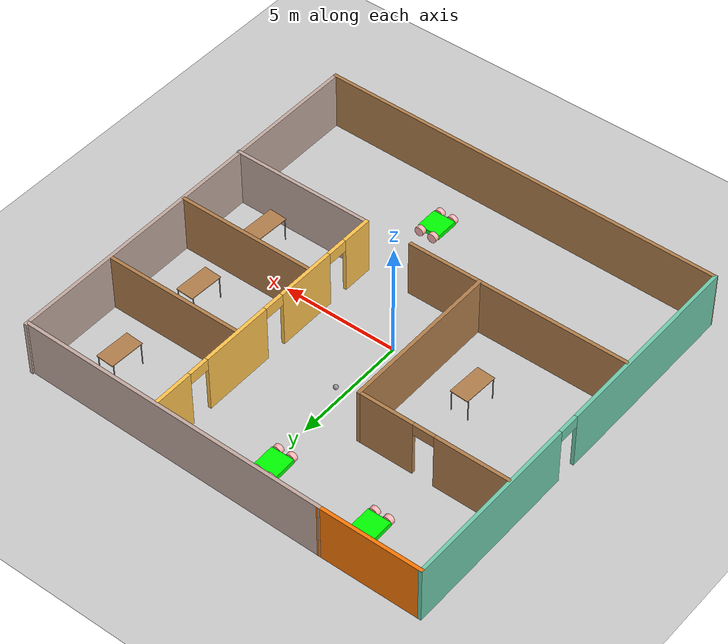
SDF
<sdf version="1.7">
 <world name="default">
  <plugin name="welcome" filename="libwelcome.so"/>
  <light name="sun" type="directional">
   <pose>0 0 10 0 -0 0</pose>
   <diffuse>0.8 0.8 0.8 1</diffuse>
   <specular>0.2 0.2 0.2 1</specular>
   <attenuation>
    <range>1000</range>
    <constant>0.9</constant>
    <linear>0.01</linear>
    <quadratic>0.001</quadratic>
   </attenuation>
   <direction>-0.5 0.1 -0.9</direction>
   <spot><inner_angle>0</inner_angle><outer_angle>0</outer_angle><falloff>0</falloff></spot>
  </light>
  <model name="ground_plane">
   <static>1</static>
   <link name="link">
    <collision name="collision">
     <geometry><plane><normal>0 0 1</normal><size>100 100</size></plane></geometry>
     <surface><friction><ode><mu>100</mu><mu2>50</mu2></ode></friction></surface>
    </collision>
    <visual name="visual">
     <cast_shadows>0</cast_shadows>
     <geometry><plane><normal>0 0 1</normal><size>100 100</size></plane></geometry>
     <material>
      <script><uri>file://media/materials/scripts/gazebo.material</uri><name>Gazebo/Grey</name></script>
     </material>
    </visual>
   </link>
  </model>
  <gravity>0 0 -9.8</gravity>
  <magnetic_field>6e-06 2.3e-05 -4.2e-05</magnetic_field>
  <atmosphere type="adiabatic"/>
  <physics name="default_physics" default="0" type="ode">
   <max_step_size>0.001</max_step_size>
   <real_time_factor>1</real_time_factor>
   <real_time_update_rate>1000</real_time_update_rate>
  </physics>
  <scene><ambient>0.4 0.4 0.4 1</ambient><background>0.7 0.7 0.7 1</background><shadows>1</shadows></scene>
  <spherical_coordinates>
   <surface_model>EARTH_WGS84</surface_model>
   <latitude_deg>0</latitude_deg>
   <longitude_deg>0</longitude_deg>
   <elevation>0</elevation>
   <heading_deg>0</heading_deg>
  </spherical_coordinates>
  <model name="small-office-with-textures">
   <pose>0.616 0.33819 0 0 -0 0</pose>
   <link name="Wall_31">
    <collision name="Wall_31_Collision">
     <geometry><box><size>13.5 0.15 2.5</size></box></geometry>
     <pose>0 0 1.25 0 -0 0</pose>
    </collision>
    <visual name="Wall_31_Visual">
     <pose>0 0 1.25 0 -0 0</pose>
     <geometry><box><size>13.5 0.15 2.5</size></box></geometry>
     <material>
      <script><uri>file://media/materials/scripts/gazebo.material</uri><name>Gazebo/Grey</name></script>
      <ambient>0.760784 0.662745 0.627451 1</ambient>
     </material>
     <meta><layer>0</layer></meta>
    </visual>
    <pose>2.10617 8.54991 0 0 0 -0.0106</pose>
   </link>
   <link name="Wall_32">
    <collision name="Wall_32_Collision">
     <geometry><box><size>17.25 0.15 2.5</size></box></geometry>
     <pose>0 0 1.25 0 -0 0</pose>
    </collision>
    <visual name="Wall_32_Visual">
     <pose>0 0 1.25 0 -0 0</pose>
     <geometry><box><size>17.25 0.15 2.5</size></box></geometry>
     <material>
      <script><uri>file://media/materials/scripts/gazebo.material</uri><name>Gazebo/Grey</name></script>
      <ambient>0.760784 0.662745 0.627451 1</ambient>
     </material>
     <meta><layer>0</layer></meta>
    </visual>
    <pose>8.78117 -9.4e-05 0 0 0 -1.5708</pose>
   </link>
   <link name="Wall_33">
    <collision name="Wall_33_Collision">
     <geometry><box><size>17.75 0.15 2.5</size></box></geometry>
     <pose>0 0 1.25 0 -0 0</pose>
    </collision>
    <visual name="Wall_33_Visual">
     <pose>0 0 1.25 0 -0 0</pose>
     <geometry><box><size>17.75 0.15 2.5</size></box></geometry>
     <material>
      <script><uri>file://media/materials/scripts/gazebo.material</uri><name>Gazebo/Wood</name></script>
      <ambient>1 1 1 1</ambient>
     </material>
     <meta><layer>0</layer></meta>
    </visual>
    <pose>-0.018829 -8.55009 0 0 -0 3.13355</pose>
   </link>
   <link name="Wall_34">
    <pose>-8.81883 0.070663 0 0 -0 1.5708</pose>
    <visual name="Wall_34_Visual_0">
     <pose>-4.29565 0 1.25 0 -0 0</pose>
     <geometry><box><size>8.65869 0.15 2.5</size></box></geometry>
     <material>
      <script><uri>file://media/materials/scripts/gazebo.material</uri><name>Gazebo/Grey</name></script>
      <ambient>0.435294 0.796078 0.67451 1</ambient>
     </material>
     <meta><layer>0</layer></meta>
    </visual>
    <collision name="Wall_34_Collision_0">
     <geometry><box><size>8.65869 0.15 2.5</size></box></geometry>
     <pose>-4.29565 0 1.25 0 -0 0</pose>
    </collision>
    <visual name="Wall_34_Visual_1">
     <pose>4.77935 0 1.25 0 -0 0</pose>
     <geometry><box><size>7.6913 0.15 2.5</size></box></geometry>
     <material>
      <script><uri>file://media/materials/scripts/gazebo.material</uri><name>Gazebo/Grey</name></script>
      <ambient>0.435294 0.796078 0.67451 1</ambient>
     </material>
     <meta><layer>0</layer></meta>
    </visual>
    <collision name="Wall_34_Collision_1">
     <geometry><box><size>7.6913 0.15 2.5</size></box></geometry>
     <pose>4.77935 0 1.25 0 -0 0</pose>
    </collision>
    <visual name="Wall_34_Visual_2">
     <pose>0.483695 0 2.25 0 -0 0</pose>
     <geometry><box><size>0.9 0.15 0.5</size></box></geometry>
     <material>
      <script><uri>file://media/materials/scripts/gazebo.material</uri><name>Gazebo/Grey</name></script>
      <ambient>0.435294 0.796078 0.67451 1</ambient>
     </material>
     <meta><layer>0</layer></meta>
    </visual>
    <collision name="Wall_34_Collision_2">
     <geometry><box><size>0.9 0.15 0.5</size></box></geometry>
     <pose>0.483695 0 2.25 0 -0 0</pose>
    </collision>
   </link>
   <link name="Wall_35">
    <collision name="Wall_35_Collision">
     <geometry><box><size>4.4 0.15 2.5</size></box></geometry>
     <pose>0 0 1.25 0 -0 0</pose>
    </collision>
    <visual name="Wall_35_Visual">
     <pose>0 0 1.25 0 -0 0</pose>
     <geometry><box><size>4.4 0.15 2.5</size></box></geometry>
     <material>
      <script><uri>file://media/materials/scripts/gazebo.material</uri><name>Gazebo/Grey</name></script>
      <ambient>0.996078 0.47451 0.0196078 1</ambient>
     </material>
     <meta><layer>0</layer></meta>
    </visual>
    <pose>-6.69383 8.62066 0 0 -0 0</pose>
   </link>
   <link name="Wall_37">
    <pose>-5.5685 3.80918 0 0 -0 0</pose>
    <visual name="Wall_37_Visual_0">
     <pose>-1.66857 0 1.25 0 -0 0</pose>
     <geometry><box><size>3.16285 0.15 2.5</size></box></geometry>
     <material>
      <script><uri>file://media/materials/scripts/gazebo.material</uri><name>Gazebo/Wood</name></script>
      <ambient>1 1 1 1</ambient>
     </material>
     <meta><layer>0</layer></meta>
    </visual>
    <collision name="Wall_37_Collision_0">
     <geometry><box><size>3.16285 0.15 2.5</size></box></geometry>
     <pose>-1.66857 0 1.25 0 -0 0</pose>
    </collision>
    <visual name="Wall_37_Visual_1">
     <pose>2.03143 0 1.25 0 -0 0</pose>
     <geometry><box><size>2.43715 0.15 2.5</size></box></geometry>
     <material>
      <script><uri>file://media/materials/scripts/gazebo.material</uri><name>Gazebo/Wood</name></script>
      <ambient>1 1 1 1</ambient>
     </material>
     <meta><layer>0</layer></meta>
    </visual>
    <collision name="Wall_37_Collision_1">
     <geometry><box><size>2.43715 0.15 2.5</size></box></geometry>
     <pose>2.03143 0 1.25 0 -0 0</pose>
    </collision>
    <visual name="Wall_37_Visual_2">
     <pose>0.362853 0 2.25 0 -0 0</pose>
     <geometry><box><size>0.9 0.15 0.5</size></box></geometry>
     <material>
      <script><uri>file://media/materials/scripts/gazebo.material</uri><name>Gazebo/Wood</name></script>
      <ambient>1 1 1 1</ambient>
     </material>
     <meta><layer>0</layer></meta>
    </visual>
    <collision name="Wall_37_Collision_2">
     <geometry><box><size>0.9 0.15 0.5</size></box></geometry>
     <pose>0.362853 0 2.25 0 -0 0</pose>
    </collision>
   </link>
   <link name="Wall_38">
    <collision name="Wall_38_Collision">
     <geometry><box><size>7 0.15 2.5</size></box></geometry>
     <pose>0 0 1.25 0 -0 0</pose>
    </collision>
    <visual name="Wall_38_Visual">
     <pose>0 0 1.25 0 -0 0</pose>
     <geometry><box><size>7 0.15 2.5</size></box></geometry>
     <material>
      <script><uri>file://media/materials/scripts/gazebo.material</uri><name>Gazebo/Wood</name></script>
      <ambient>0.760784 0.662745 0.627451 1</ambient>
     </material>
     <meta><layer>0</layer></meta>
    </visual>
    <pose>-2.3935 0.384183 0 0 0 -1.5708</pose>
   </link>
   <link name="Wall_39">
    <collision name="Wall_39_Collision">
     <geometry><box><size>6.5 0.15 2.5</size></box></geometry>
     <pose>0 0 1.25 0 -0 0</pose>
    </collision>
    <visual name="Wall_39_Visual">
     <pose>0 0 1.25 0 -0 0</pose>
     <geometry><box><size>6.5 0.15 2.5</size></box></geometry>
     <material>
      <script><uri>file://media/materials/scripts/gazebo.material</uri><name>Gazebo/Wood</name></script>
      <ambient>0.760784 0.662745 0.627451 1</ambient>
     </material>
     <meta><layer>0</layer></meta>
    </visual>
    <pose>-5.5685 -3.04082 0 0 -0 3.14159</pose>
   </link>
   <link name="Wall_44">
    <collision name="Wall_44_Collision">
     <geometry><box><size>3.25 0.15 2.5</size></box></geometry>
     <pose>0 0 1.25 0 -0 0</pose>
    </collision>
    <visual name="Wall_44_Visual">
     <pose>0 0 1.25 0 -0 0</pose>
     <geometry><box><size>3.25 0.15 2.5</size></box></geometry>
     <material>
      <script><uri>file://media/materials/scripts/gazebo.material</uri><name>Gazebo/Wood</name></script>
      <ambient>0.760784 0.662745 0.627451 1</ambient>
     </material>
     <meta><layer>0</layer></meta>
    </visual>
    <pose>-0.843495 -3.04082 0 0 -0 0</pose>
   </link>
   <link name="Wall_46">
    <pose>2.71915 2.73339 0 0 0 -1.5708</pose>
    <visual name="Wall_46_Visual_0">
     <pose>-4.91152 0 1.25 0 -0 0</pose>
     <geometry><box><size>1.67695 0.15 2.5</size></box></geometry>
     <material>
      <script><uri>file://media/materials/scripts/gazebo.material</uri><name>Gazebo/Grey</name></script>
      <ambient>1 0.764706 0.305882 1</ambient>
     </material>
     <meta><layer>0</layer></meta>
    </visual>
    <collision name="Wall_46_Collision_0">
     <geometry><box><size>1.67695 0.15 2.5</size></box></geometry>
     <pose>-4.91152 0 1.25 0 -0 0</pose>
    </collision>
    <visual name="Wall_46_Visual_1">
     <pose>-1.60647 0 1.25 0 -0 0</pose>
     <geometry><box><size>3.13315 0.15 2.5</size></box></geometry>
     <material>
      <script><uri>file://media/materials/scripts/gazebo.material</uri><name>Gazebo/Grey</name></script>
      <ambient>1 0.764706 0.305882 1</ambient>
     </material>
     <meta><layer>0</layer></meta>
    </visual>
    <collision name="Wall_46_Collision_1">
     <geometry><box><size>3.13315 0.15 2.5</size></box></geometry>
     <pose>-1.60647 0 1.25 0 -0 0</pose>
    </collision>
    <visual name="Wall_46_Visual_2">
     <pose>2.17903 0 1.25 0 -0 0</pose>
     <geometry><box><size>2.63785 0.15 2.5</size></box></geometry>
     <material>
      <script><uri>file://media/materials/scripts/gazebo.material</uri><name>Gazebo/Grey</name></script>
      <ambient>1 0.764706 0.305882 1</ambient>
     </material>
     <meta><layer>0</layer></meta>
    </visual>
    <collision name="Wall_46_Collision_2">
     <geometry><box><size>2.63785 0.15 2.5</size></box></geometry>
     <pose>2.17903 0 1.25 0 -0 0</pose>
    </collision>
    <visual name="Wall_46_Visual_3">
     <pose>5.07398 0 1.25 0 -0 0</pose>
     <geometry><box><size>1.35204 0.15 2.5</size></box></geometry>
     <material>
      <script><uri>file://media/materials/scripts/gazebo.material</uri><name>Gazebo/Grey</name></script>
      <ambient>1 0.764706 0.305882 1</ambient>
     </material>
     <meta><layer>0</layer></meta>
    </visual>
    <collision name="Wall_46_Collision_3">
     <geometry><box><size>1.35204 0.15 2.5</size></box></geometry>
     <pose>5.07398 0 1.25 0 -0 0</pose>
    </collision>
    <visual name="Wall_46_Visual_4">
     <pose>-3.62304 0 2.25 0 -0 0</pose>
     <geometry><box><size>0.9 0.15 0.5</size></box></geometry>
     <material>
      <script><uri>file://media/materials/scripts/gazebo.material</uri><name>Gazebo/Grey</name></script>
      <ambient>1 0.764706 0.305882 1</ambient>
     </material>
     <meta><layer>0</layer></meta>
    </visual>
    <collision name="Wall_46_Collision_4">
     <geometry><box><size>0.9 0.15 0.5</size></box></geometry>
     <pose>-3.62304 0 2.25 0 -0 0</pose>
    </collision>
    <visual name="Wall_46_Visual_5">
     <pose>0.410107 0 2.25 0 -0 0</pose>
     <geometry><box><size>0.9 0.15 0.5</size></box></geometry>
     <material>
      <script><uri>file://media/materials/scripts/gazebo.material</uri><name>Gazebo/Grey</name></script>
      <ambient>1 0.764706 0.305882 1</ambient>
     </material>
     <meta><layer>0</layer></meta>
    </visual>
    <collision name="Wall_46_Collision_5">
     <geometry><box><size>0.9 0.15 0.5</size></box></geometry>
     <pose>0.410107 0 2.25 0 -0 0</pose>
    </collision>
    <visual name="Wall_46_Visual_6">
     <pose>3.94796 0 2.25 0 -0 0</pose>
     <geometry><box><size>0.9 0.15 0.5</size></box></geometry>
     <material>
      <script><uri>file://media/materials/scripts/gazebo.material</uri><name>Gazebo/Grey</name></script>
      <ambient>1 0.764706 0.305882 1</ambient>
     </material>
     <meta><layer>0</layer></meta>
    </visual>
    <collision name="Wall_46_Collision_6">
     <geometry><box><size>0.9 0.15 0.5</size></box></geometry>
     <pose>3.94796 0 2.25 0 -0 0</pose>
    </collision>
   </link>
   <link name="Wall_47">
    <collision name="Wall_47_Collision">
     <geometry><box><size>6.25 0.15 2.5</size></box></geometry>
     <pose>0 0 1.25 0 -0 0</pose>
    </collision>
    <visual name="Wall_47_Visual">
     <pose>0 0 1.25 0 -0 0</pose>
     <geometry><box><size>6.25 0.15 2.5</size></box></geometry>
     <material>
      <script><uri>file://media/materials/scripts/gazebo.material</uri><name>Gazebo/Grey</name></script>
      <ambient>0.760784 0.662745 0.627451 1</ambient>
     </material>
     <meta><layer>0</layer></meta>
    </visual>
    <pose>5.76915 -2.94161 0 0 -0 0</pose>
   </link>
   <link name="Wall_49">
    <collision name="Wall_49_Collision">
     <geometry><box><size>6 0.15 2.5</size></box></geometry>
     <pose>0 0 1.25 0 -0 0</pose>
    </collision>
    <visual name="Wall_49_Visual">
     <pose>0 0 1.25 0 -0 0</pose>
     <geometry><box><size>6 0.15 2.5</size></box></geometry>
     <material>
      <script><uri>file://media/materials/scripts/gazebo.material</uri><name>Gazebo/Wood</name></script>
      <ambient>0.760784 0.662745 0.627451 1</ambient>
     </material>
     <meta><layer>0</layer></meta>
    </visual>
    <pose>5.78566 4.23373 0 0 -0 0</pose>
   </link>
   <link name="Wall_51">
    <collision name="Wall_51_Collision">
     <geometry><box><size>6 0.15 2.5</size></box></geometry>
     <pose>0 0 1.25 0 -0 0</pose>
    </collision>
    <visual name="Wall_51_Visual">
     <pose>0 0 1.25 0 -0 0</pose>
     <geometry><box><size>6 0.15 2.5</size></box></geometry>
     <material>
      <script><uri>file://media/materials/scripts/gazebo.material</uri><name>Gazebo/Wood</name></script>
      <ambient>0.760784 0.662745 0.627451 1</ambient>
     </material>
     <meta><layer>0</layer></meta>
    </visual>
    <pose>5.78566 0.27133 0 0 -0 0</pose>
   </link>
   <static>1</static>
  </model>
  <model name="table_0">
   <static>1</static>
   <link name="link">
    <collision name="surface">
     <pose>0 0 1 0 -0 0</pose>
     <geometry><box><size>1.5 0.8 0.03</size></box></geometry>
     <surface><friction><ode><mu>0.6</mu><mu2>0.6</mu2></ode></friction></surface>
    </collision>
    <visual name="visual1">
     <pose>0 0 1 0 -0 0</pose>
     <geometry><box><size>1.5 0.8 0.03</size></box></geometry>
     <material>
      <script><uri>file://media/materials/scripts/gazebo.material</uri><name>Gazebo/Wood</name></script>
     </material>
    </visual>
    <collision name="front_left_leg">
     <pose>0.68 0.38 0.5 0 -0 0</pose>
     <geometry><cylinder><radius>0.02</radius><length>1</length></cylinder></geometry>
    </collision>
    <visual name="front_left_leg">
     <pose>0.68 0.38 0.5 0 -0 0</pose>
     <geometry><cylinder><radius>0.02</radius><length>1</length></cylinder></geometry>
     <material>
      <script><uri>file://media/materials/scripts/gazebo.material</uri><name>Gazebo/Grey</name></script>
     </material>
    </visual>
    <collision name="front_right_leg">
     <pose>0.68 -0.38 0.5 0 -0 0</pose>
     <geometry><cylinder><radius>0.02</radius><length>1</length></cylinder></geometry>
    </collision>
    <visual name="front_right_leg">
     <pose>0.68 -0.38 0.5 0 -0 0</pose>
     <geometry><cylinder><radius>0.02</radius><length>1</length></cylinder></geometry>
     <material>
      <script><uri>file://media/materials/scripts/gazebo.material</uri><name>Gazebo/Grey</name></script>
     </material>
    </visual>
    <collision name="back_right_leg">
     <pose>-0.68 -0.38 0.5 0 -0 0</pose>
     <geometry><cylinder><radius>0.02</radius><length>1</length></cylinder></geometry>
    </collision>
    <visual name="back_right_leg">
     <pose>-0.68 -0.38 0.5 0 -0 0</pose>
     <geometry><cylinder><radius>0.02</radius><length>1</length></cylinder></geometry>
     <material>
      <script><uri>file://media/materials/scripts/gazebo.material</uri><name>Gazebo/Grey</name></script>
     </material>
    </visual>
    <collision name="back_left_leg">
     <pose>-0.68 0.38 0.5 0 -0 0</pose>
     <geometry><cylinder><radius>0.02</radius><length>1</length></cylinder></geometry>
    </collision>
    <visual name="back_left_leg">
     <pose>-0.68 0.38 0.5 0 -0 0</pose>
     <geometry><cylinder><radius>0.02</radius><length>1</length></cylinder></geometry>
     <material>
      <script><uri>file://media/materials/scripts/gazebo.material</uri><name>Gazebo/Grey</name></script>
     </material>
    </visual>
   </link>
   <pose>6.91504 -1.05286 0.346112 0.000206 -0.004127 -1.62077</pose>
  </model>
  <model name="table_0_clone">
   <static>1</static>
   <link name="link">
    <collision name="surface">
     <pose>0 0 1 0 -0 0</pose>
     <geometry><box><size>1.5 0.8 0.03</size></box></geometry>
     <surface><friction><ode><mu>0.6</mu><mu2>0.6</mu2></ode></friction></surface>
    </collision>
    <visual name="visual1">
     <pose>0 0 1 0 -0 0</pose>
     <geometry><box><size>1.5 0.8 0.03</size></box></geometry>
     <material>
      <script><uri>file://media/materials/scripts/gazebo.material</uri><name>Gazebo/Wood</name></script>
     </material>
    </visual>
    <collision name="front_left_leg">
     <pose>0.68 0.38 0.5 0 -0 0</pose>
     <geometry><cylinder><radius>0.02</radius><length>1</length></cylinder></geometry>
    </collision>
    <visual name="front_left_leg">
     <pose>0.68 0.38 0.5 0 -0 0</pose>
     <geometry><cylinder><radius>0.02</radius><length>1</length></cylinder></geometry>
     <material>
      <script><uri>file://media/materials/scripts/gazebo.material</uri><name>Gazebo/Grey</name></script>
     </material>
    </visual>
    <collision name="front_right_leg">
     <pose>0.68 -0.38 0.5 0 -0 0</pose>
     <geometry><cylinder><radius>0.02</radius><length>1</length></cylinder></geometry>
    </collision>
    <visual name="front_right_leg">
     <pose>0.68 -0.38 0.5 0 -0 0</pose>
     <geometry><cylinder><radius>0.02</radius><length>1</length></cylinder></geometry>
     <material>
      <script><uri>file://media/materials/scripts/gazebo.material</uri><name>Gazebo/Grey</name></script>
     </material>
    </visual>
    <collision name="back_right_leg">
     <pose>-0.68 -0.38 0.5 0 -0 0</pose>
     <geometry><cylinder><radius>0.02</radius><length>1</length></cylinder></geometry>
    </collision>
    <visual name="back_right_leg">
     <pose>-0.68 -0.38 0.5 0 -0 0</pose>
     <geometry><cylinder><radius>0.02</radius><length>1</length></cylinder></geometry>
     <material>
      <script><uri>file://media/materials/scripts/gazebo.material</uri><name>Gazebo/Grey</name></script>
     </material>
    </visual>
    <collision name="back_left_leg">
     <pose>-0.68 0.38 0.5 0 -0 0</pose>
     <geometry><cylinder><radius>0.02</radius><length>1</length></cylinder></geometry>
    </collision>
    <visual name="back_left_leg">
     <pose>-0.68 0.38 0.5 0 -0 0</pose>
     <geometry><cylinder><radius>0.02</radius><length>1</length></cylinder></geometry>
     <material>
      <script><uri>file://media/materials/scripts/gazebo.material</uri><name>Gazebo/Grey</name></script>
     </material>
    </visual>
   </link>
   <pose>6.80691 2.77332 0.346112 0.000206 -0.004127 -1.62077</pose>
  </model>
  <model name="table_0_clone_0">
   <static>1</static>
   <link name="link">
    <collision name="surface">
     <pose>0 0 1 0 -0 0</pose>
     <geometry><box><size>1.5 0.8 0.03</size></box></geometry>
     <surface><friction><ode><mu>0.6</mu><mu2>0.6</mu2></ode></friction></surface>
    </collision>
    <visual name="visual1">
     <pose>0 0 1 0 -0 0</pose>
     <geometry><box><size>1.5 0.8 0.03</size></box></geometry>
     <material>
      <script><uri>file://media/materials/scripts/gazebo.material</uri><name>Gazebo/Wood</name></script>
     </material>
    </visual>
    <collision name="front_left_leg">
     <pose>0.68 0.38 0.5 0 -0 0</pose>
     <geometry><cylinder><radius>0.02</radius><length>1</length></cylinder></geometry>
    </collision>
    <visual name="front_left_leg">
     <pose>0.68 0.38 0.5 0 -0 0</pose>
     <geometry><cylinder><radius>0.02</radius><length>1</length></cylinder></geometry>
     <material>
      <script><uri>file://media/materials/scripts/gazebo.material</uri><name>Gazebo/Grey</name></script>
     </material>
    </visual>
    <collision name="front_right_leg">
     <pose>0.68 -0.38 0.5 0 -0 0</pose>
     <geometry><cylinder><radius>0.02</radius><length>1</length></cylinder></geometry>
    </collision>
    <visual name="front_right_leg">
     <pose>0.68 -0.38 0.5 0 -0 0</pose>
     <geometry><cylinder><radius>0.02</radius><length>1</length></cylinder></geometry>
     <material>
      <script><uri>file://media/materials/scripts/gazebo.material</uri><name>Gazebo/Grey</name></script>
     </material>
    </visual>
    <collision name="back_right_leg">
     <pose>-0.68 -0.38 0.5 0 -0 0</pose>
     <geometry><cylinder><radius>0.02</radius><length>1</length></cylinder></geometry>
    </collision>
    <visual name="back_right_leg">
     <pose>-0.68 -0.38 0.5 0 -0 0</pose>
     <geometry><cylinder><radius>0.02</radius><length>1</length></cylinder></geometry>
     <material>
      <script><uri>file://media/materials/scripts/gazebo.material</uri><name>Gazebo/Grey</name></script>
     </material>
    </visual>
    <collision name="back_left_leg">
     <pose>-0.68 0.38 0.5 0 -0 0</pose>
     <geometry><cylinder><radius>0.02</radius><length>1</length></cylinder></geometry>
    </collision>
    <visual name="back_left_leg">
     <pose>-0.68 0.38 0.5 0 -0 0</pose>
     <geometry><cylinder><radius>0.02</radius><length>1</length></cylinder></geometry>
     <material>
      <script><uri>file://media/materials/scripts/gazebo.material</uri><name>Gazebo/Grey</name></script>
     </material>
    </visual>
   </link>
   <pose>6.78526 7.02709 0.346112 0.000206 -0.004127 -1.62077</pose>
  </model>
  <model name="table_0_clone_1">
   <static>1</static>
   <link name="link">
    <collision name="surface">
     <pose>0 0 1 0 -0 0</pose>
     <geometry><box><size>1.5 0.8 0.03</size></box></geometry>
     <surface><friction><ode><mu>0.6</mu><mu2>0.6</mu2></ode></friction></surface>
    </collision>
    <visual name="visual1">
     <pose>0 0 1 0 -0 0</pose>
     <geometry><box><size>1.5 0.8 0.03</size></box></geometry>
     <material>
      <script><uri>file://media/materials/scripts/gazebo.material</uri><name>Gazebo/Wood</name></script>
     </material>
    </visual>
    <collision name="front_left_leg">
     <pose>0.68 0.38 0.5 0 -0 0</pose>
     <geometry><cylinder><radius>0.02</radius><length>1</length></cylinder></geometry>
    </collision>
    <visual name="front_left_leg">
     <pose>0.68 0.38 0.5 0 -0 0</pose>
     <geometry><cylinder><radius>0.02</radius><length>1</length></cylinder></geometry>
     <material>
      <script><uri>file://media/materials/scripts/gazebo.material</uri><name>Gazebo/Grey</name></script>
     </material>
    </visual>
    <collision name="front_right_leg">
     <pose>0.68 -0.38 0.5 0 -0 0</pose>
     <geometry><cylinder><radius>0.02</radius><length>1</length></cylinder></geometry>
    </collision>
    <visual name="front_right_leg">
     <pose>0.68 -0.38 0.5 0 -0 0</pose>
     <geometry><cylinder><radius>0.02</radius><length>1</length></cylinder></geometry>
     <material>
      <script><uri>file://media/materials/scripts/gazebo.material</uri><name>Gazebo/Grey</name></script>
     </material>
    </visual>
    <collision name="back_right_leg">
     <pose>-0.68 -0.38 0.5 0 -0 0</pose>
     <geometry><cylinder><radius>0.02</radius><length>1</length></cylinder></geometry>
    </collision>
    <visual name="back_right_leg">
     <pose>-0.68 -0.38 0.5 0 -0 0</pose>
     <geometry><cylinder><radius>0.02</radius><length>1</length></cylinder></geometry>
     <material>
      <script><uri>file://media/materials/scripts/gazebo.material</uri><name>Gazebo/Grey</name></script>
     </material>
    </visual>
    <collision name="back_left_leg">
     <pose>-0.68 0.38 0.5 0 -0 0</pose>
     <geometry><cylinder><radius>0.02</radius><length>1</length></cylinder></geometry>
    </collision>
    <visual name="back_left_leg">
     <pose>-0.68 0.38 0.5 0 -0 0</pose>
     <geometry><cylinder><radius>0.02</radius><length>1</length></cylinder></geometry>
     <material>
      <script><uri>file://media/materials/scripts/gazebo.material</uri><name>Gazebo/Grey</name></script>
     </material>
    </visual>
   </link>
   <pose>-3.98054 0.594288 0.346112 0.000206 -0.004127 -1.62077</pose>
  </model>
  <model name="cabinet">
   <static>1</static>
   <link name="cabinet_bottom_plate">
    <inertial>
     <pose>0 0 -1 0 -0 0</pose>
     <inertia><ixx>2.05</ixx><ixy>0</ixy><ixz>0</ixz><iyy>2.05</iyy><iyz>0</iyz><izz>2.05</izz></inertia>
     <mass>25</mass>
    </inertial>
    <collision name="cabinet_bottom_plate_geom">
     <pose>0 0 0.01 0 -0 0</pose>
     <geometry><box><size>0.45 0.45 0.02</size></box></geometry>
    </collision>
    <visual name="cabinet_bottom_plate_geom_visual">
     <pose>0 0 0.01 0 -0 0</pose>
     <geometry><box><size>0.45 0.45 0.02</size></box></geometry>
     <material>
      <script><uri>file://media/materials/scripts/gazebo.material</uri><name>Gazebo/Wood</name></script>
     </material>
    </visual>
    <collision name="cabinet_bottom_plate_geom_cabinet_back_plate">
     <pose>0.235 0 0.51 0 -0 0</pose>
     <geometry><box><size>0.02 0.45 1.02</size></box></geometry>
    </collision>
    <visual name="cabinet_bottom_plate_geom_cabinet_back_plate_visual">
     <pose>0.235 0 0.51 0 -0 0</pose>
     <geometry><box><size>0.02 0.45 1.02</size></box></geometry>
     <material>
      <script><uri>file://media/materials/scripts/gazebo.material</uri><name>Gazebo/Wood</name></script>
     </material>
    </visual>
    <collision name="cabinet_bottom_plate_geom_cabinet_left_plate">
     <pose>0 0.235 0.51 0 -0 0</pose>
     <geometry><box><size>0.45 0.02 1.02</size></box></geometry>
    </collision>
    <visual name="cabinet_bottom_plate_geom_cabinet_left_plate_visual">
     <pose>0 0.235 0.51 0 -0 0</pose>
     <geometry><box><size>0.45 0.02 1.02</size></box></geometry>
     <material>
      <script><uri>file://media/materials/scripts/gazebo.material</uri><name>Gazebo/Wood</name></script>
     </material>
    </visual>
    <collision name="cabinet_bottom_plate_geom_cabinet_middle_plate">
     <pose>0 0 0.51 0 -0 0</pose>
     <geometry><box><size>0.45 0.45 0.02</size></box></geometry>
    </collision>
    <visual name="cabinet_bottom_plate_geom_cabinet_middle_plate_visual">
     <pose>0 0 0.51 0 -0 0</pose>
     <geometry><box><size>0.45 0.45 0.02</size></box></geometry>
     <material>
      <script><uri>file://media/materials/scripts/gazebo.material</uri><name>Gazebo/Wood</name></script>
     </material>
    </visual>
    <collision name="cabinet_bottom_plate_geom_cabinet_right_plate">
     <pose>0 -0.235 0.51 0 -0 0</pose>
     <geometry><box><size>0.45 0.02 1.02</size></box></geometry>
    </collision>
    <visual name="cabinet_bottom_plate_geom_cabinet_right_plate_visual">
     <pose>0 -0.235 0.51 0 -0 0</pose>
     <geometry><box><size>0.45 0.02 1.02</size></box></geometry>
     <material>
      <script><uri>file://media/materials/scripts/gazebo.material</uri><name>Gazebo/Wood</name></script>
     </material>
    </visual>
    <collision name="cabinet_bottom_plate_geom_cabinet_top_plate">
     <pose>0 0 1.01 0 -0 0</pose>
     <geometry><box><size>0.45 0.45 0.02</size></box></geometry>
    </collision>
    <visual name="cabinet_bottom_plate_geom_cabinet_top_plate_visual">
     <pose>0 0 1.01 0 -0 0</pose>
     <geometry><box><size>0.45 0.45 0.02</size></box></geometry>
     <material>
      <script><uri>file://media/materials/scripts/gazebo.material</uri><name>Gazebo/Wood</name></script>
     </material>
    </visual>
   </link>
   <pose>-7.68746 8.65206 0 0 -0 0</pose>
  </model>
  <model name="bookshelf">
   <static>1</static>
   <link name="link">
    <inertial><mass>1</mass></inertial>
    <collision name="back">
     <pose>0 0.005 0.6 0 -0 0</pose>
     <geometry><box><size>0.9 0.01 1.2</size></box></geometry>
    </collision>
    <visual name="visual1">
     <pose>0 0.005 0.6 0 -0 0</pose>
     <geometry><box><size>0.9 0.01 1.2</size></box></geometry>
     <material>
      <script><uri>file://media/materials/scripts/gazebo.material</uri><name>Gazebo/Wood</name></script>
     </material>
    </visual>
    <collision name="left_side">
     <pose>0.45 -0.195 0.6 0 -0 0</pose>
     <geometry><box><size>0.02 0.4 1.2</size></box></geometry>
    </collision>
    <visual name="visual2">
     <pose>0.45 -0.195 0.6 0 -0 0</pose>
     <geometry><box><size>0.02 0.4 1.2</size></box></geometry>
     <material>
      <script><uri>file://media/materials/scripts/gazebo.material</uri><name>Gazebo/Wood</name></script>
     </material>
    </visual>
    <collision name="right_side">
     <pose>-0.45 -0.195 0.6 0 -0 0</pose>
     <geometry><box><size>0.02 0.4 1.2</size></box></geometry>
    </collision>
    <visual name="visual3">
     <pose>-0.45 -0.195 0.6 0 -0 0</pose>
     <geometry><box><size>0.02 0.4 1.2</size></box></geometry>
     <material>
      <script><uri>file://media/materials/scripts/gazebo.material</uri><name>Gazebo/Wood</name></script>
     </material>
    </visual>
    <collision name="bottom">
     <pose>0 -0.195 0.03 0 -0 0</pose>
     <geometry><box><size>0.88 0.4 0.06</size></box></geometry>
    </collision>
    <visual name="visual4">
     <pose>0 -0.195 0.03 0 -0 0</pose>
     <geometry><box><size>0.88 0.4 0.06</size></box></geometry>
     <material>
      <script><uri>file://media/materials/scripts/gazebo.material</uri><name>Gazebo/Wood</name></script>
     </material>
    </visual>
    <collision name="top">
     <pose>0 -0.195 1.19 0 -0 0</pose>
     <geometry><box><size>0.88 0.4 0.02</size></box></geometry>
    </collision>
    <visual name="visual5">
     <pose>0 -0.195 1.19 0 -0 0</pose>
     <geometry><box><size>0.88 0.4 0.02</size></box></geometry>
     <material>
      <script><uri>file://media/materials/scripts/gazebo.material</uri><name>Gazebo/Wood</name></script>
     </material>
    </visual>
    <collision name="low_shelf">
     <pose>0 -0.195 0.43 0 -0 0</pose>
     <geometry><box><size>0.88 0.4 0.02</size></box></geometry>
    </collision>
    <visual name="visual6">
     <pose>0 -0.195 0.43 0 -0 0</pose>
     <geometry><box><size>0.88 0.4 0.02</size></box></geometry>
     <material>
      <script><uri>file://media/materials/scripts/gazebo.material</uri><name>Gazebo/Wood</name></script>
     </material>
    </visual>
    <collision name="high_shelf">
     <pose>0 -0.195 0.8 0 -0 0</pose>
     <geometry><box><size>0.88 0.4 0.02</size></box></geometry>
    </collision>
    <visual name="visual7">
     <pose>0 -0.195 0.8 0 -0 0</pose>
     <geometry><box><size>0.88 0.4 0.02</size></box></geometry>
     <material>
      <script><uri>file://media/materials/scripts/gazebo.material</uri><name>Gazebo/Wood</name></script>
     </material>
    </visual>
   </link>
   <pose>4.06665 8.8562 0 0 -0 0</pose>
  </model>
  <model name="AWDRobot">
   <link name="link_0">
    <inertial>
     <mass>1</mass>
     <inertia>
      <ixx>0.166667</ixx>
      <ixy>0</ixy>
      <ixz>0</ixz>
      <iyy>0.166667</iyy>
      <iyz>0</iyz>
      <izz>0.166667</izz>
     </inertia>
    </inertial>
    <visual name="visual">
     <geometry><box><size>1 1 0.2</size></box></geometry>
     <material>
      <lighting>1</lighting>
      <script><uri>file://media/materials/scripts/gazebo.material</uri><name>Gazebo/Grey</name></script>
      <shader type="pixel"><normal_map>__default__</normal_map></shader>
      <ambient>0 1 0 1</ambient>
      <diffuse>0 1 0 1</diffuse>
      <specular>0.01 0.01 0.01 1</specular>
      <emissive>0 0 0 1</emissive>
     </material>
    </visual>
    <collision name="collision">
     <geometry><box><size>1 1 0.2</size></box></geometry>
     <surface>
      <friction>
       <ode><mu>1</mu><mu2>1</mu2><fdir1>0 0 0</fdir1><slip1>0</slip1><slip2>0</slip2></ode>
       <torsional>
        <coefficient>1</coefficient>
        <patch_radius>0</patch_radius>
        <surface_radius>0</surface_radius>
        <use_patch_radius>1</use_patch_radius>
        <ode><slip>0</slip></ode>
       </torsional>
      </friction>
      <bounce><restitution_coefficient>0</restitution_coefficient><threshold>1e+06</threshold></bounce>
      <contact>
       <collide_without_contact>0</collide_without_contact>
       <collide_without_contact_bitmask>1</collide_without_contact_bitmask>
       <collide_bitmask>1</collide_bitmask>
       <ode>
        <soft_cfm>0</soft_cfm>
        <soft_erp>0.2</soft_erp>
        <kp>1e+13</kp>
        <kd>1</kd>
        <max_vel>0.01</max_vel>
        <min_depth>0</min_depth>
       </ode>
       <bullet>
        <split_impulse>1</split_impulse>
        <split_impulse_penetration_threshold>-0.01</split_impulse_penetration_threshold>
        <soft_cfm>0</soft_cfm>
        <soft_erp>0.2</soft_erp>
        <kp>1e+13</kp>
        <kd>1</kd>
       </bullet>
      </contact>
     </surface>
    </collision>
   </link>
   <link name="link_1">
    <pose>0.3 -0.600019 0 1.5707 -0 0</pose>
    <inertial>
     <mass>1</mass>
     <inertia><ixx>0.145833</ixx><ixy>0</ixy><ixz>0</ixz><iyy>0.145833</iyy><iyz>0</iyz><izz>0.125</izz></inertia>
    </inertial>
    <visual name="visual">
     <geometry><cylinder><radius>0.2</radius><length>0.2</length></cylinder></geometry>
     <material>
      <lighting>1</lighting>
      <script><uri>file://media/materials/scripts/gazebo.material</uri><name>Gazebo/Grey</name></script>
      <shader type="pixel"><normal_map>__default__</normal_map></shader>
      <ambient>1 0.3 0.3 1</ambient>
      <diffuse>1 0.7 0.7 1</diffuse>
      <specular>0.01 0.01 0.01 1</specular>
      <emissive>0 0 0 1</emissive>
     </material>
    </visual>
    <collision name="collision">
     <geometry><cylinder><radius>0.2</radius><length>0.2</length></cylinder></geometry>
     <surface>
      <friction>
       <ode><mu>1</mu><mu2>1</mu2><fdir1>0 0 0</fdir1><slip1>0</slip1><slip2>0</slip2></ode>
       <torsional>
        <coefficient>1</coefficient>
        <patch_radius>0</patch_radius>
        <surface_radius>0</surface_radius>
        <use_patch_radius>1</use_patch_radius>
        <ode><slip>0</slip></ode>
       </torsional>
      </friction>
      <bounce><restitution_coefficient>0</restitution_coefficient><threshold>1e+06</threshold></bounce>
      <contact>
       <collide_without_contact>0</collide_without_contact>
       <collide_without_contact_bitmask>1</collide_without_contact_bitmask>
       <collide_bitmask>1</collide_bitmask>
       <ode>
        <soft_cfm>0</soft_cfm>
        <soft_erp>0.2</soft_erp>
        <kp>1e+13</kp>
        <kd>1</kd>
        <max_vel>0.01</max_vel>
        <min_depth>0</min_depth>
       </ode>
       <bullet>
        <split_impulse>1</split_impulse>
        <split_impulse_penetration_threshold>-0.01</split_impulse_penetration_threshold>
        <soft_cfm>0</soft_cfm>
        <soft_erp>0.2</soft_erp>
        <kp>1e+13</kp>
        <kd>1</kd>
       </bullet>
      </contact>
     </surface>
    </collision>
   </link>
   <link name="link_1_clone">
    <pose>-0.3 -0.600019 0 1.5707 -0 0</pose>
    <inertial>
     <mass>1</mass>
     <inertia><ixx>0.145833</ixx><ixy>0</ixy><ixz>0</ixz><iyy>0.145833</iyy><iyz>0</iyz><izz>0.125</izz></inertia>
    </inertial>
    <visual name="visual">
     <geometry><cylinder><radius>0.2</radius><length>0.2</length></cylinder></geometry>
     <material>
      <lighting>1</lighting>
      <script><uri>file://media/materials/scripts/gazebo.material</uri><name>Gazebo/Grey</name></script>
      <shader type="pixel"><normal_map>__default__</normal_map></shader>
      <ambient>1 0.3 0.3 1</ambient>
      <diffuse>1 0.7 0.7 1</diffuse>
      <specular>0.01 0.01 0.01 1</specular>
      <emissive>0 0 0 1</emissive>
     </material>
    </visual>
    <collision name="collision">
     <geometry><cylinder><radius>0.2</radius><length>0.2</length></cylinder></geometry>
     <surface>
      <friction>
       <ode><mu>1</mu><mu2>1</mu2><fdir1>0 0 0</fdir1><slip1>0</slip1><slip2>0</slip2></ode>
       <torsional>
        <coefficient>1</coefficient>
        <patch_radius>0</patch_radius>
        <surface_radius>0</surface_radius>
        <use_patch_radius>1</use_patch_radius>
        <ode><slip>0</slip></ode>
       </torsional>
      </friction>
      <bounce><restitution_coefficient>0</restitution_coefficient><threshold>1e+06</threshold></bounce>
      <contact>
       <collide_without_contact>0</collide_without_contact>
       <collide_without_contact_bitmask>1</collide_without_contact_bitmask>
       <collide_bitmask>1</collide_bitmask>
       <ode>
        <soft_cfm>0</soft_cfm>
        <soft_erp>0.2</soft_erp>
        <kp>1e+13</kp>
        <kd>1</kd>
        <max_vel>0.01</max_vel>
        <min_depth>0</min_depth>
       </ode>
       <bullet>
        <split_impulse>1</split_impulse>
        <split_impulse_penetration_threshold>-0.01</split_impulse_penetration_threshold>
        <soft_cfm>0</soft_cfm>
        <soft_erp>0.2</soft_erp>
        <kp>1e+13</kp>
        <kd>1</kd>
       </bullet>
      </contact>
     </surface>
    </collision>
   </link>
   <link name="link_1_clone_0">
    <pose>-0.3 0.600019 0 1.5707 -0 0</pose>
    <inertial>
     <mass>1</mass>
     <inertia><ixx>0.145833</ixx><ixy>0</ixy><ixz>0</ixz><iyy>0.145833</iyy><iyz>0</iyz><izz>0.125</izz></inertia>
    </inertial>
    <visual name="visual">
     <geometry><cylinder><radius>0.2</radius><length>0.2</length></cylinder></geometry>
     <material>
      <lighting>1</lighting>
      <script><uri>file://media/materials/scripts/gazebo.material</uri><name>Gazebo/Grey</name></script>
      <shader type="pixel"><normal_map>__default__</normal_map></shader>
      <ambient>1 0.3 0.3 1</ambient>
      <diffuse>1 0.7 0.7 1</diffuse>
      <specular>0.01 0.01 0.01 1</specular>
      <emissive>0 0 0 1</emissive>
     </material>
    </visual>
    <collision name="collision">
     <geometry><cylinder><radius>0.2</radius><length>0.2</length></cylinder></geometry>
     <surface>
      <friction>
       <ode><mu>1</mu><mu2>1</mu2><fdir1>0 0 0</fdir1><slip1>0</slip1><slip2>0</slip2></ode>
       <torsional>
        <coefficient>1</coefficient>
        <patch_radius>0</patch_radius>
        <surface_radius>0</surface_radius>
        <use_patch_radius>1</use_patch_radius>
        <ode><slip>0</slip></ode>
       </torsional>
      </friction>
      <bounce><restitution_coefficient>0</restitution_coefficient><threshold>1e+06</threshold></bounce>
      <contact>
       <collide_without_contact>0</collide_without_contact>
       <collide_without_contact_bitmask>1</collide_without_contact_bitmask>
       <collide_bitmask>1</collide_bitmask>
       <ode>
        <soft_cfm>0</soft_cfm>
        <soft_erp>0.2</soft_erp>
        <kp>1e+13</kp>
        <kd>1</kd>
        <max_vel>0.01</max_vel>
        <min_depth>0</min_depth>
       </ode>
       <bullet>
        <split_impulse>1</split_impulse>
        <split_impulse_penetration_threshold>-0.01</split_impulse_penetration_threshold>
        <soft_cfm>0</soft_cfm>
        <soft_erp>0.2</soft_erp>
        <kp>1e+13</kp>
        <kd>1</kd>
       </bullet>
      </contact>
     </surface>
    </collision>
   </link>
   <link name="link_1_clone_1">
    <pose>0.3 0.600019 0 1.5707 -0 0</pose>
    <inertial>
     <mass>1</mass>
     <inertia><ixx>0.145833</ixx><ixy>0</ixy><ixz>0</ixz><iyy>0.145833</iyy><iyz>0</iyz><izz>0.125</izz></inertia>
    </inertial>
    <visual name="visual">
     <geometry><cylinder><radius>0.2</radius><length>0.2</length></cylinder></geometry>
     <material>
      <lighting>1</lighting>
      <script><uri>file://media/materials/scripts/gazebo.material</uri><name>Gazebo/Grey</name></script>
      <shader type="pixel"><normal_map>__default__</normal_map></shader>
      <ambient>1 0.3 0.3 1</ambient>
      <diffuse>1 0.7 0.7 1</diffuse>
      <specular>0.01 0.01 0.01 1</specular>
      <emissive>0 0 0 1</emissive>
     </material>
    </visual>
    <collision name="collision">
     <geometry><cylinder><radius>0.2</radius><length>0.2</length></cylinder></geometry>
     <surface>
      <friction>
       <ode><mu>1</mu><mu2>1</mu2><fdir1>0 0 0</fdir1><slip1>0</slip1><slip2>0</slip2></ode>
       <torsional>
        <coefficient>1</coefficient>
        <patch_radius>0</patch_radius>
        <surface_radius>0</surface_radius>
        <use_patch_radius>1</use_patch_radius>
        <ode><slip>0</slip></ode>
       </torsional>
      </friction>
      <bounce><restitution_coefficient>0</restitution_coefficient><threshold>1e+06</threshold></bounce>
      <contact>
       <collide_without_contact>0</collide_without_contact>
       <collide_without_contact_bitmask>1</collide_without_contact_bitmask>
       <collide_bitmask>1</collide_bitmask>
       <ode>
        <soft_cfm>0</soft_cfm>
        <soft_erp>0.2</soft_erp>
        <kp>1e+13</kp>
        <kd>1</kd>
        <max_vel>0.01</max_vel>
        <min_depth>0</min_depth>
       </ode>
       <bullet>
        <split_impulse>1</split_impulse>
        <split_impulse_penetration_threshold>-0.01</split_impulse_penetration_threshold>
        <soft_cfm>0</soft_cfm>
        <soft_erp>0.2</soft_erp>
        <kp>1e+13</kp>
        <kd>1</kd>
       </bullet>
      </contact>
     </surface>
    </collision>
   </link>
   <joint name="link_0_JOINT_1" type="revolute">
    <parent>link_0</parent>
    <child>link_1_clone</child>
    <axis>
     <xyz>0 0 1</xyz>
     <limit>
      <lower>-1.79769e+308</lower>
      <upper>1.79769e+308</upper>
      <effort>-1</effort>
      <velocity>-1</velocity>
     </limit>
     <dynamics>
      <spring_reference>0</spring_reference>
      <spring_stiffness>0</spring_stiffness>
      <damping>0</damping>
     </dynamics>
    </axis>
    <physics>
     <ode><limit><cfm>0</cfm><erp>0.2</erp></limit><suspension><cfm>0</cfm><erp>0.2</erp></suspension></ode>
    </physics>
   </joint>
   <joint name="link_0_JOINT_2" type="revolute">
    <parent>link_0</parent>
    <child>link_1</child>
    <axis>
     <xyz>0 0 1</xyz>
     <limit>
      <lower>-1.79769e+308</lower>
      <upper>1.79769e+308</upper>
      <effort>-1</effort>
      <velocity>-1</velocity>
     </limit>
     <dynamics>
      <spring_reference>0</spring_reference>
      <spring_stiffness>0</spring_stiffness>
      <damping>0</damping>
     </dynamics>
    </axis>
    <physics>
     <ode><limit><cfm>0</cfm><erp>0.2</erp></limit><suspension><cfm>0</cfm><erp>0.2</erp></suspension></ode>
    </physics>
   </joint>
   <joint name="link_0_JOINT_3" type="revolute">
    <parent>link_0</parent>
    <child>link_1_clone_0</child>
    <axis>
     <xyz>0 0 1</xyz>
     <limit>
      <lower>-1.79769e+308</lower>
      <upper>1.79769e+308</upper>
      <effort>-1</effort>
      <velocity>-1</velocity>
     </limit>
     <dynamics>
      <spring_reference>0</spring_reference>
      <spring_stiffness>0</spring_stiffness>
      <damping>0</damping>
     </dynamics>
    </axis>
    <physics>
     <ode><limit><cfm>0</cfm><erp>0.2</erp></limit><suspension><cfm>0</cfm><erp>0.2</erp></suspension></ode>
    </physics>
   </joint>
   <joint name="link_0_JOINT_4" type="revolute">
    <parent>link_0</parent>
    <child>link_1_clone_1</child>
    <axis>
     <xyz>0 0 1</xyz>
     <limit>
      <lower>-1.79769e+308</lower>
      <upper>1.79769e+308</upper>
      <effort>-1</effort>
      <velocity>-1</velocity>
     </limit>
     <dynamics>
      <spring_reference>0</spring_reference>
      <spring_stiffness>0</spring_stiffness>
      <damping>0</damping>
     </dynamics>
    </axis>
    <physics>
     <ode><limit><cfm>0</cfm><erp>0.2</erp></limit><suspension><cfm>0</cfm><erp>0.2</erp></suspension></ode>
    </physics>
   </joint>
   <static>0</static>
   <pose>-0.249181 6.96899 0.200008 -3e-06 -0 0.021169</pose>
  </model>
  <model name="AWDRobot_clone">
   <link name="link_0">
    <inertial>
     <mass>1</mass>
     <inertia>
      <ixx>0.166667</ixx>
      <ixy>0</ixy>
      <ixz>0</ixz>
      <iyy>0.166667</iyy>
      <iyz>0</iyz>
      <izz>0.166667</izz>
     </inertia>
    </inertial>
    <visual name="visual">
     <geometry><box><size>1 1 0.2</size></box></geometry>
     <material>
      <lighting>1</lighting>
      <script><uri>file://media/materials/scripts/gazebo.material</uri><name>Gazebo/Grey</name></script>
      <shader type="pixel"><normal_map>__default__</normal_map></shader>
      <ambient>0 1 0 1</ambient>
      <diffuse>0 1 0 1</diffuse>
      <specular>0.01 0.01 0.01 1</specular>
      <emissive>0 0 0 1</emissive>
     </material>
    </visual>
    <collision name="collision">
     <geometry><box><size>1 1 0.2</size></box></geometry>
     <surface>
      <friction>
       <ode><mu>1</mu><mu2>1</mu2><fdir1>0 0 0</fdir1><slip1>0</slip1><slip2>0</slip2></ode>
       <torsional>
        <coefficient>1</coefficient>
        <patch_radius>0</patch_radius>
        <surface_radius>0</surface_radius>
        <use_patch_radius>1</use_patch_radius>
        <ode><slip>0</slip></ode>
       </torsional>
      </friction>
      <bounce><restitution_coefficient>0</restitution_coefficient><threshold>1e+06</threshold></bounce>
      <contact>
       <collide_without_contact>0</collide_without_contact>
       <collide_without_contact_bitmask>1</collide_without_contact_bitmask>
       <collide_bitmask>1</collide_bitmask>
       <ode>
        <soft_cfm>0</soft_cfm>
        <soft_erp>0.2</soft_erp>
        <kp>1e+13</kp>
        <kd>1</kd>
        <max_vel>0.01</max_vel>
        <min_depth>0</min_depth>
       </ode>
       <bullet>
        <split_impulse>1</split_impulse>
        <split_impulse_penetration_threshold>-0.01</split_impulse_penetration_threshold>
        <soft_cfm>0</soft_cfm>
        <soft_erp>0.2</soft_erp>
        <kp>1e+13</kp>
        <kd>1</kd>
       </bullet>
      </contact>
     </surface>
    </collision>
   </link>
   <link name="link_1">
    <pose>0.3 -0.600019 0 1.5707 -0 0</pose>
    <inertial>
     <mass>1</mass>
     <inertia><ixx>0.145833</ixx><ixy>0</ixy><ixz>0</ixz><iyy>0.145833</iyy><iyz>0</iyz><izz>0.125</izz></inertia>
    </inertial>
    <visual name="visual">
     <geometry><cylinder><radius>0.2</radius><length>0.2</length></cylinder></geometry>
     <material>
      <lighting>1</lighting>
      <script><uri>file://media/materials/scripts/gazebo.material</uri><name>Gazebo/Grey</name></script>
      <shader type="pixel"><normal_map>__default__</normal_map></shader>
      <ambient>1 0.3 0.3 1</ambient>
      <diffuse>1 0.7 0.7 1</diffuse>
      <specular>0.01 0.01 0.01 1</specular>
      <emissive>0 0 0 1</emissive>
     </material>
    </visual>
    <collision name="collision">
     <geometry><cylinder><radius>0.2</radius><length>0.2</length></cylinder></geometry>
     <surface>
      <friction>
       <ode><mu>1</mu><mu2>1</mu2><fdir1>0 0 0</fdir1><slip1>0</slip1><slip2>0</slip2></ode>
       <torsional>
        <coefficient>1</coefficient>
        <patch_radius>0</patch_radius>
        <surface_radius>0</surface_radius>
        <use_patch_radius>1</use_patch_radius>
        <ode><slip>0</slip></ode>
       </torsional>
      </friction>
      <bounce><restitution_coefficient>0</restitution_coefficient><threshold>1e+06</threshold></bounce>
      <contact>
       <collide_without_contact>0</collide_without_contact>
       <collide_without_contact_bitmask>1</collide_without_contact_bitmask>
       <collide_bitmask>1</collide_bitmask>
       <ode>
        <soft_cfm>0</soft_cfm>
        <soft_erp>0.2</soft_erp>
        <kp>1e+13</kp>
        <kd>1</kd>
        <max_vel>0.01</max_vel>
        <min_depth>0</min_depth>
       </ode>
       <bullet>
        <split_impulse>1</split_impulse>
        <split_impulse_penetration_threshold>-0.01</split_impulse_penetration_threshold>
        <soft_cfm>0</soft_cfm>
        <soft_erp>0.2</soft_erp>
        <kp>1e+13</kp>
        <kd>1</kd>
       </bullet>
      </contact>
     </surface>
    </collision>
   </link>
   <link name="link_1_clone">
    <pose>-0.3 -0.600019 0 1.5707 -0 0</pose>
    <inertial>
     <mass>1</mass>
     <inertia><ixx>0.145833</ixx><ixy>0</ixy><ixz>0</ixz><iyy>0.145833</iyy><iyz>0</iyz><izz>0.125</izz></inertia>
    </inertial>
    <visual name="visual">
     <geometry><cylinder><radius>0.2</radius><length>0.2</length></cylinder></geometry>
     <material>
      <lighting>1</lighting>
      <script><uri>file://media/materials/scripts/gazebo.material</uri><name>Gazebo/Grey</name></script>
      <shader type="pixel"><normal_map>__default__</normal_map></shader>
      <ambient>1 0.3 0.3 1</ambient>
      <diffuse>1 0.7 0.7 1</diffuse>
      <specular>0.01 0.01 0.01 1</specular>
      <emissive>0 0 0 1</emissive>
     </material>
    </visual>
    <collision name="collision">
     <geometry><cylinder><radius>0.2</radius><length>0.2</length></cylinder></geometry>
     <surface>
      <friction>
       <ode><mu>1</mu><mu2>1</mu2><fdir1>0 0 0</fdir1><slip1>0</slip1><slip2>0</slip2></ode>
       <torsional>
        <coefficient>1</coefficient>
        <patch_radius>0</patch_radius>
        <surface_radius>0</surface_radius>
        <use_patch_radius>1</use_patch_radius>
        <ode><slip>0</slip></ode>
       </torsional>
      </friction>
      <bounce><restitution_coefficient>0</restitution_coefficient><threshold>1e+06</threshold></bounce>
      <contact>
       <collide_without_contact>0</collide_without_contact>
       <collide_without_contact_bitmask>1</collide_without_contact_bitmask>
       <collide_bitmask>1</collide_bitmask>
       <ode>
        <soft_cfm>0</soft_cfm>
        <soft_erp>0.2</soft_erp>
        <kp>1e+13</kp>
        <kd>1</kd>
        <max_vel>0.01</max_vel>
        <min_depth>0</min_depth>
       </ode>
       <bullet>
        <split_impulse>1</split_impulse>
        <split_impulse_penetration_threshold>-0.01</split_impulse_penetration_threshold>
        <soft_cfm>0</soft_cfm>
        <soft_erp>0.2</soft_erp>
        <kp>1e+13</kp>
        <kd>1</kd>
       </bullet>
      </contact>
     </surface>
    </collision>
   </link>
   <link name="link_1_clone_0">
    <pose>-0.3 0.600019 0 1.5707 -0 0</pose>
    <inertial>
     <mass>1</mass>
     <inertia><ixx>0.145833</ixx><ixy>0</ixy><ixz>0</ixz><iyy>0.145833</iyy><iyz>0</iyz><izz>0.125</izz></inertia>
    </inertial>
    <visual name="visual">
     <geometry><cylinder><radius>0.2</radius><length>0.2</length></cylinder></geometry>
     <material>
      <lighting>1</lighting>
      <script><uri>file://media/materials/scripts/gazebo.material</uri><name>Gazebo/Grey</name></script>
      <shader type="pixel"><normal_map>__default__</normal_map></shader>
      <ambient>1 0.3 0.3 1</ambient>
      <diffuse>1 0.7 0.7 1</diffuse>
      <specular>0.01 0.01 0.01 1</specular>
      <emissive>0 0 0 1</emissive>
     </material>
    </visual>
    <collision name="collision">
     <geometry><cylinder><radius>0.2</radius><length>0.2</length></cylinder></geometry>
     <surface>
      <friction>
       <ode><mu>1</mu><mu2>1</mu2><fdir1>0 0 0</fdir1><slip1>0</slip1><slip2>0</slip2></ode>
       <torsional>
        <coefficient>1</coefficient>
        <patch_radius>0</patch_radius>
        <surface_radius>0</surface_radius>
        <use_patch_radius>1</use_patch_radius>
        <ode><slip>0</slip></ode>
       </torsional>
      </friction>
      <bounce><restitution_coefficient>0</restitution_coefficient><threshold>1e+06</threshold></bounce>
      <contact>
       <collide_without_contact>0</collide_without_contact>
       <collide_without_contact_bitmask>1</collide_without_contact_bitmask>
       <collide_bitmask>1</collide_bitmask>
       <ode>
        <soft_cfm>0</soft_cfm>
        <soft_erp>0.2</soft_erp>
        <kp>1e+13</kp>
        <kd>1</kd>
        <max_vel>0.01</max_vel>
        <min_depth>0</min_depth>
       </ode>
       <bullet>
        <split_impulse>1</split_impulse>
        <split_impulse_penetration_threshold>-0.01</split_impulse_penetration_threshold>
        <soft_cfm>0</soft_cfm>
        <soft_erp>0.2</soft_erp>
        <kp>1e+13</kp>
        <kd>1</kd>
       </bullet>
      </contact>
     </surface>
    </collision>
   </link>
   <link name="link_1_clone_1">
    <pose>0.3 0.600019 0 1.5707 -0 0</pose>
    <inertial>
     <mass>1</mass>
     <inertia><ixx>0.145833</ixx><ixy>0</ixy><ixz>0</ixz><iyy>0.145833</iyy><iyz>0</iyz><izz>0.125</izz></inertia>
    </inertial>
    <visual name="visual">
     <geometry><cylinder><radius>0.2</radius><length>0.2</length></cylinder></geometry>
     <material>
      <lighting>1</lighting>
      <script><uri>file://media/materials/scripts/gazebo.material</uri><name>Gazebo/Grey</name></script>
      <shader type="pixel"><normal_map>__default__</normal_map></shader>
      <ambient>1 0.3 0.3 1</ambient>
      <diffuse>1 0.7 0.7 1</diffuse>
      <specular>0.01 0.01 0.01 1</specular>
      <emissive>0 0 0 1</emissive>
     </material>
    </visual>
    <collision name="collision">
     <geometry><cylinder><radius>0.2</radius><length>0.2</length></cylinder></geometry>
     <surface>
      <friction>
       <ode><mu>1</mu><mu2>1</mu2><fdir1>0 0 0</fdir1><slip1>0</slip1><slip2>0</slip2></ode>
       <torsional>
        <coefficient>1</coefficient>
        <patch_radius>0</patch_radius>
        <surface_radius>0</surface_radius>
        <use_patch_radius>1</use_patch_radius>
        <ode><slip>0</slip></ode>
       </torsional>
      </friction>
      <bounce><restitution_coefficient>0</restitution_coefficient><threshold>1e+06</threshold></bounce>
      <contact>
       <collide_without_contact>0</collide_without_contact>
       <collide_without_contact_bitmask>1</collide_without_contact_bitmask>
       <collide_bitmask>1</collide_bitmask>
       <ode>
        <soft_cfm>0</soft_cfm>
        <soft_erp>0.2</soft_erp>
        <kp>1e+13</kp>
        <kd>1</kd>
        <max_vel>0.01</max_vel>
        <min_depth>0</min_depth>
       </ode>
       <bullet>
        <split_impulse>1</split_impulse>
        <split_impulse_penetration_threshold>-0.01</split_impulse_penetration_threshold>
        <soft_cfm>0</soft_cfm>
        <soft_erp>0.2</soft_erp>
        <kp>1e+13</kp>
        <kd>1</kd>
       </bullet>
      </contact>
     </surface>
    </collision>
   </link>
   <joint name="link_0_JOINT_1" type="revolute">
    <parent>link_0</parent>
    <child>link_1_clone</child>
    <axis>
     <xyz>0 0 1</xyz>
     <limit>
      <lower>-1.79769e+308</lower>
      <upper>1.79769e+308</upper>
      <effort>-1</effort>
      <velocity>-1</velocity>
     </limit>
     <dynamics>
      <spring_reference>0</spring_reference>
      <spring_stiffness>0</spring_stiffness>
      <damping>0</damping>
     </dynamics>
    </axis>
    <physics>
     <ode><limit><cfm>0</cfm><erp>0.2</erp></limit><suspension><cfm>0</cfm><erp>0.2</erp></suspension></ode>
    </physics>
   </joint>
   <joint name="link_0_JOINT_2" type="revolute">
    <parent>link_0</parent>
    <child>link_1</child>
    <axis>
     <xyz>0 0 1</xyz>
     <limit>
      <lower>-1.79769e+308</lower>
      <upper>1.79769e+308</upper>
      <effort>-1</effort>
      <velocity>-1</velocity>
     </limit>
     <dynamics>
      <spring_reference>0</spring_reference>
      <spring_stiffness>0</spring_stiffness>
      <damping>0</damping>
     </dynamics>
    </axis>
    <physics>
     <ode><limit><cfm>0</cfm><erp>0.2</erp></limit><suspension><cfm>0</cfm><erp>0.2</erp></suspension></ode>
    </physics>
   </joint>
   <joint name="link_0_JOINT_3" type="revolute">
    <parent>link_0</parent>
    <child>link_1_clone_0</child>
    <axis>
     <xyz>0 0 1</xyz>
     <limit>
      <lower>-1.79769e+308</lower>
      <upper>1.79769e+308</upper>
      <effort>-1</effort>
      <velocity>-1</velocity>
     </limit>
     <dynamics>
      <spring_reference>0</spring_reference>
      <spring_stiffness>0</spring_stiffness>
      <damping>0</damping>
     </dynamics>
    </axis>
    <physics>
     <ode><limit><cfm>0</cfm><erp>0.2</erp></limit><suspension><cfm>0</cfm><erp>0.2</erp></suspension></ode>
    </physics>
   </joint>
   <joint name="link_0_JOINT_4" type="revolute">
    <parent>link_0</parent>
    <child>link_1_clone_1</child>
    <axis>
     <xyz>0 0 1</xyz>
     <limit>
      <lower>-1.79769e+308</lower>
      <upper>1.79769e+308</upper>
      <effort>-1</effort>
      <velocity>-1</velocity>
     </limit>
     <dynamics>
      <spring_reference>0</spring_reference>
      <spring_stiffness>0</spring_stiffness>
      <damping>0</damping>
     </dynamics>
    </axis>
    <physics>
     <ode><limit><cfm>0</cfm><erp>0.2</erp></limit><suspension><cfm>0</cfm><erp>0.2</erp></suspension></ode>
    </physics>
   </joint>
   <static>0</static>
   <pose>-4.59596 7.0777 0.200005 0 -1.5e-05 -0.000731</pose>
  </model>
  <model name="AWDRobot_clone_0">
   <link name="link_0">
    <inertial>
     <mass>1</mass>
     <inertia>
      <ixx>0.166667</ixx>
      <ixy>0</ixy>
      <ixz>0</ixz>
      <iyy>0.166667</iyy>
      <iyz>0</iyz>
      <izz>0.166667</izz>
     </inertia>
    </inertial>
    <visual name="visual">
     <geometry><box><size>1 1 0.2</size></box></geometry>
     <material>
      <lighting>1</lighting>
      <script><uri>file://media/materials/scripts/gazebo.material</uri><name>Gazebo/Grey</name></script>
      <shader type="pixel"><normal_map>__default__</normal_map></shader>
      <ambient>0 1 0 1</ambient>
      <diffuse>0 1 0 1</diffuse>
      <specular>0.01 0.01 0.01 1</specular>
      <emissive>0 0 0 1</emissive>
     </material>
    </visual>
    <collision name="collision">
     <geometry><box><size>1 1 0.2</size></box></geometry>
     <surface>
      <friction>
       <ode><mu>1</mu><mu2>1</mu2><fdir1>0 0 0</fdir1><slip1>0</slip1><slip2>0</slip2></ode>
       <torsional>
        <coefficient>1</coefficient>
        <patch_radius>0</patch_radius>
        <surface_radius>0</surface_radius>
        <use_patch_radius>1</use_patch_radius>
        <ode><slip>0</slip></ode>
       </torsional>
      </friction>
      <bounce><restitution_coefficient>0</restitution_coefficient><threshold>1e+06</threshold></bounce>
      <contact>
       <collide_without_contact>0</collide_without_contact>
       <collide_without_contact_bitmask>1</collide_without_contact_bitmask>
       <collide_bitmask>1</collide_bitmask>
       <ode>
        <soft_cfm>0</soft_cfm>
        <soft_erp>0.2</soft_erp>
        <kp>1e+13</kp>
        <kd>1</kd>
        <max_vel>0.01</max_vel>
        <min_depth>0</min_depth>
       </ode>
       <bullet>
        <split_impulse>1</split_impulse>
        <split_impulse_penetration_threshold>-0.01</split_impulse_penetration_threshold>
        <soft_cfm>0</soft_cfm>
        <soft_erp>0.2</soft_erp>
        <kp>1e+13</kp>
        <kd>1</kd>
       </bullet>
      </contact>
     </surface>
    </collision>
   </link>
   <link name="link_1">
    <pose>0.3 -0.600019 0 1.5707 -0 0</pose>
    <inertial>
     <mass>1</mass>
     <inertia><ixx>0.145833</ixx><ixy>0</ixy><ixz>0</ixz><iyy>0.145833</iyy><iyz>0</iyz><izz>0.125</izz></inertia>
    </inertial>
    <visual name="visual">
     <geometry><cylinder><radius>0.2</radius><length>0.2</length></cylinder></geometry>
     <material>
      <lighting>1</lighting>
      <script><uri>file://media/materials/scripts/gazebo.material</uri><name>Gazebo/Grey</name></script>
      <shader type="pixel"><normal_map>__default__</normal_map></shader>
      <ambient>1 0.3 0.3 1</ambient>
      <diffuse>1 0.7 0.7 1</diffuse>
      <specular>0.01 0.01 0.01 1</specular>
      <emissive>0 0 0 1</emissive>
     </material>
    </visual>
    <collision name="collision">
     <geometry><cylinder><radius>0.2</radius><length>0.2</length></cylinder></geometry>
     <surface>
      <friction>
       <ode><mu>1</mu><mu2>1</mu2><fdir1>0 0 0</fdir1><slip1>0</slip1><slip2>0</slip2></ode>
       <torsional>
        <coefficient>1</coefficient>
        <patch_radius>0</patch_radius>
        <surface_radius>0</surface_radius>
        <use_patch_radius>1</use_patch_radius>
        <ode><slip>0</slip></ode>
       </torsional>
      </friction>
      <bounce><restitution_coefficient>0</restitution_coefficient><threshold>1e+06</threshold></bounce>
      <contact>
       <collide_without_contact>0</collide_without_contact>
       <collide_without_contact_bitmask>1</collide_without_contact_bitmask>
       <collide_bitmask>1</collide_bitmask>
       <ode>
        <soft_cfm>0</soft_cfm>
        <soft_erp>0.2</soft_erp>
        <kp>1e+13</kp>
        <kd>1</kd>
        <max_vel>0.01</max_vel>
        <min_depth>0</min_depth>
       </ode>
       <bullet>
        <split_impulse>1</split_impulse>
        <split_impulse_penetration_threshold>-0.01</split_impulse_penetration_threshold>
        <soft_cfm>0</soft_cfm>
        <soft_erp>0.2</soft_erp>
        <kp>1e+13</kp>
        <kd>1</kd>
       </bullet>
      </contact>
     </surface>
    </collision>
   </link>
   <link name="link_1_clone">
    <pose>-0.3 -0.600019 0 1.5707 -0 0</pose>
    <inertial>
     <mass>1</mass>
     <inertia><ixx>0.145833</ixx><ixy>0</ixy><ixz>0</ixz><iyy>0.145833</iyy><iyz>0</iyz><izz>0.125</izz></inertia>
    </inertial>
    <visual name="visual">
     <geometry><cylinder><radius>0.2</radius><length>0.2</length></cylinder></geometry>
     <material>
      <lighting>1</lighting>
      <script><uri>file://media/materials/scripts/gazebo.material</uri><name>Gazebo/Grey</name></script>
      <shader type="pixel"><normal_map>__default__</normal_map></shader>
      <ambient>1 0.3 0.3 1</ambient>
      <diffuse>1 0.7 0.7 1</diffuse>
      <specular>0.01 0.01 0.01 1</specular>
      <emissive>0 0 0 1</emissive>
     </material>
    </visual>
    <collision name="collision">
     <geometry><cylinder><radius>0.2</radius><length>0.2</length></cylinder></geometry>
     <surface>
      <friction>
       <ode><mu>1</mu><mu2>1</mu2><fdir1>0 0 0</fdir1><slip1>0</slip1><slip2>0</slip2></ode>
       <torsional>
        <coefficient>1</coefficient>
        <patch_radius>0</patch_radius>
        <surface_radius>0</surface_radius>
        <use_patch_radius>1</use_patch_radius>
        <ode><slip>0</slip></ode>
       </torsional>
      </friction>
      <bounce><restitution_coefficient>0</restitution_coefficient><threshold>1e+06</threshold></bounce>
      <contact>
       <collide_without_contact>0</collide_without_contact>
       <collide_without_contact_bitmask>1</collide_without_contact_bitmask>
       <collide_bitmask>1</collide_bitmask>
       <ode>
        <soft_cfm>0</soft_cfm>
        <soft_erp>0.2</soft_erp>
        <kp>1e+13</kp>
        <kd>1</kd>
        <max_vel>0.01</max_vel>
        <min_depth>0</min_depth>
       </ode>
       <bullet>
        <split_impulse>1</split_impulse>
        <split_impulse_penetration_threshold>-0.01</split_impulse_penetration_threshold>
        <soft_cfm>0</soft_cfm>
        <soft_erp>0.2</soft_erp>
        <kp>1e+13</kp>
        <kd>1</kd>
       </bullet>
      </contact>
     </surface>
    </collision>
   </link>
   <link name="link_1_clone_0">
    <pose>-0.3 0.600019 0 1.5707 -0 0</pose>
    <inertial>
     <mass>1</mass>
     <inertia><ixx>0.145833</ixx><ixy>0</ixy><ixz>0</ixz><iyy>0.145833</iyy><iyz>0</iyz><izz>0.125</izz></inertia>
    </inertial>
    <visual name="visual">
     <geometry><cylinder><radius>0.2</radius><length>0.2</length></cylinder></geometry>
     <material>
      <lighting>1</lighting>
      <script><uri>file://media/materials/scripts/gazebo.material</uri><name>Gazebo/Grey</name></script>
      <shader type="pixel"><normal_map>__default__</normal_map></shader>
      <ambient>1 0.3 0.3 1</ambient>
      <diffuse>1 0.7 0.7 1</diffuse>
      <specular>0.01 0.01 0.01 1</specular>
      <emissive>0 0 0 1</emissive>
     </material>
    </visual>
    <collision name="collision">
     <geometry><cylinder><radius>0.2</radius><length>0.2</length></cylinder></geometry>
     <surface>
      <friction>
       <ode><mu>1</mu><mu2>1</mu2><fdir1>0 0 0</fdir1><slip1>0</slip1><slip2>0</slip2></ode>
       <torsional>
        <coefficient>1</coefficient>
        <patch_radius>0</patch_radius>
        <surface_radius>0</surface_radius>
        <use_patch_radius>1</use_patch_radius>
        <ode><slip>0</slip></ode>
       </torsional>
      </friction>
      <bounce><restitution_coefficient>0</restitution_coefficient><threshold>1e+06</threshold></bounce>
      <contact>
       <collide_without_contact>0</collide_without_contact>
       <collide_without_contact_bitmask>1</collide_without_contact_bitmask>
       <collide_bitmask>1</collide_bitmask>
       <ode>
        <soft_cfm>0</soft_cfm>
        <soft_erp>0.2</soft_erp>
        <kp>1e+13</kp>
        <kd>1</kd>
        <max_vel>0.01</max_vel>
        <min_depth>0</min_depth>
       </ode>
       <bullet>
        <split_impulse>1</split_impulse>
        <split_impulse_penetration_threshold>-0.01</split_impulse_penetration_threshold>
        <soft_cfm>0</soft_cfm>
        <soft_erp>0.2</soft_erp>
        <kp>1e+13</kp>
        <kd>1</kd>
       </bullet>
      </contact>
     </surface>
    </collision>
   </link>
   <link name="link_1_clone_1">
    <pose>0.3 0.600019 0 1.5707 -0 0</pose>
    <inertial>
     <mass>1</mass>
     <inertia><ixx>0.145833</ixx><ixy>0</ixy><ixz>0</ixz><iyy>0.145833</iyy><iyz>0</iyz><izz>0.125</izz></inertia>
    </inertial>
    <visual name="visual">
     <geometry><cylinder><radius>0.2</radius><length>0.2</length></cylinder></geometry>
     <material>
      <lighting>1</lighting>
      <script><uri>file://media/materials/scripts/gazebo.material</uri><name>Gazebo/Grey</name></script>
      <shader type="pixel"><normal_map>__default__</normal_map></shader>
      <ambient>1 0.3 0.3 1</ambient>
      <diffuse>1 0.7 0.7 1</diffuse>
      <specular>0.01 0.01 0.01 1</specular>
      <emissive>0 0 0 1</emissive>
     </material>
    </visual>
    <collision name="collision">
     <geometry><cylinder><radius>0.2</radius><length>0.2</length></cylinder></geometry>
     <surface>
      <friction>
       <ode><mu>1</mu><mu2>1</mu2><fdir1>0 0 0</fdir1><slip1>0</slip1><slip2>0</slip2></ode>
       <torsional>
        <coefficient>1</coefficient>
        <patch_radius>0</patch_radius>
        <surface_radius>0</surface_radius>
        <use_patch_radius>1</use_patch_radius>
        <ode><slip>0</slip></ode>
       </torsional>
      </friction>
      <bounce><restitution_coefficient>0</restitution_coefficient><threshold>1e+06</threshold></bounce>
      <contact>
       <collide_without_contact>0</collide_without_contact>
       <collide_without_contact_bitmask>1</collide_without_contact_bitmask>
       <collide_bitmask>1</collide_bitmask>
       <ode>
        <soft_cfm>0</soft_cfm>
        <soft_erp>0.2</soft_erp>
        <kp>1e+13</kp>
        <kd>1</kd>
        <max_vel>0.01</max_vel>
        <min_depth>0</min_depth>
       </ode>
       <bullet>
        <split_impulse>1</split_impulse>
        <split_impulse_penetration_threshold>-0.01</split_impulse_penetration_threshold>
        <soft_cfm>0</soft_cfm>
        <soft_erp>0.2</soft_erp>
        <kp>1e+13</kp>
        <kd>1</kd>
       </bullet>
      </contact>
     </surface>
    </collision>
   </link>
   <joint name="link_0_JOINT_1" type="revolute">
    <parent>link_0</parent>
    <child>link_1_clone</child>
    <axis>
     <xyz>0 0 1</xyz>
     <limit>
      <lower>-1.79769e+308</lower>
      <upper>1.79769e+308</upper>
      <effort>-1</effort>
      <velocity>-1</velocity>
     </limit>
     <dynamics>
      <spring_reference>0</spring_reference>
      <spring_stiffness>0</spring_stiffness>
      <damping>0</damping>
     </dynamics>
    </axis>
    <physics>
     <ode><limit><cfm>0</cfm><erp>0.2</erp></limit><suspension><cfm>0</cfm><erp>0.2</erp></suspension></ode>
    </physics>
   </joint>
   <joint name="link_0_JOINT_2" type="revolute">
    <parent>link_0</parent>
    <child>link_1</child>
    <axis>
     <xyz>0 0 1</xyz>
     <limit>
      <lower>-1.79769e+308</lower>
      <upper>1.79769e+308</upper>
      <effort>-1</effort>
      <velocity>-1</velocity>
     </limit>
     <dynamics>
      <spring_reference>0</spring_reference>
      <spring_stiffness>0</spring_stiffness>
      <damping>0</damping>
     </dynamics>
    </axis>
    <physics>
     <ode><limit><cfm>0</cfm><erp>0.2</erp></limit><suspension><cfm>0</cfm><erp>0.2</erp></suspension></ode>
    </physics>
   </joint>
   <joint name="link_0_JOINT_3" type="revolute">
    <parent>link_0</parent>
    <child>link_1_clone_0</child>
    <axis>
     <xyz>0 0 1</xyz>
     <limit>
      <lower>-1.79769e+308</lower>
      <upper>1.79769e+308</upper>
      <effort>-1</effort>
      <velocity>-1</velocity>
     </limit>
     <dynamics>
      <spring_reference>0</spring_reference>
      <spring_stiffness>0</spring_stiffness>
      <damping>0</damping>
     </dynamics>
    </axis>
    <physics>
     <ode><limit><cfm>0</cfm><erp>0.2</erp></limit><suspension><cfm>0</cfm><erp>0.2</erp></suspension></ode>
    </physics>
   </joint>
   <joint name="link_0_JOINT_4" type="revolute">
    <parent>link_0</parent>
    <child>link_1_clone_1</child>
    <axis>
     <xyz>0 0 1</xyz>
     <limit>
      <lower>-1.79769e+308</lower>
      <upper>1.79769e+308</upper>
      <effort>-1</effort>
      <velocity>-1</velocity>
     </limit>
     <dynamics>
      <spring_reference>0</spring_reference>
      <spring_stiffness>0</spring_stiffness>
      <damping>0</damping>
     </dynamics>
    </axis>
    <physics>
     <ode><limit><cfm>0</cfm><erp>0.2</erp></limit><suspension><cfm>0</cfm><erp>0.2</erp></suspension></ode>
    </physics>
   </joint>
   <static>0</static>
   <pose>2.64262 -5.97544 0.20001 0 1e-06 0.000435</pose>
  </model>
  <model name="my_ball">
   <link name="link_0">
    <inertial>
     <mass>1</mass>
     <inertia><ixx>0.1</ixx><ixy>0</ixy><ixz>0</ixz><iyy>0.1</iyy><iyz>0</iyz><izz>0.1</izz></inertia>
    </inertial>
    <visual name="visual">
     <geometry><sphere><radius>0.1</radius></sphere></geometry>
     <material>
      <lighting>1</lighting>
      <script><uri>file://media/materials/scripts/gazebo.material</uri><name>Gazebo/Grey</name></script>
      <shader type="pixel"><normal_map>__default__</normal_map></shader>
      <ambient>1 1 1 1</ambient>
      <diffuse>1 1 1 1</diffuse>
      <specular>1 1 1 1</specular>
      <emissive>1 1 1 1</emissive>
     </material>
    </visual>
    <collision name="collision">
     <geometry><sphere><radius>0.1</radius></sphere></geometry>
     <surface>
      <friction>
       <ode><mu>1</mu><mu2>1</mu2><fdir1>0 0 0</fdir1><slip1>0</slip1><slip2>0</slip2></ode>
       <torsional>
        <coefficient>1</coefficient>
        <patch_radius>0</patch_radius>
        <surface_radius>0</surface_radius>
        <use_patch_radius>1</use_patch_radius>
        <ode><slip>0</slip></ode>
       </torsional>
      </friction>
      <bounce><restitution_coefficient>0</restitution_coefficient><threshold>1e+06</threshold></bounce>
      <contact>
       <collide_without_contact>0</collide_without_contact>
       <collide_without_contact_bitmask>1</collide_without_contact_bitmask>
       <collide_bitmask>1</collide_bitmask>
       <ode>
        <soft_cfm>0</soft_cfm>
        <soft_erp>0.2</soft_erp>
        <kp>1e+13</kp>
        <kd>1</kd>
        <max_vel>0.01</max_vel>
        <min_depth>0</min_depth>
       </ode>
       <bullet>
        <split_impulse>1</split_impulse>
        <split_impulse_penetration_threshold>-0.01</split_impulse_penetration_threshold>
        <soft_cfm>0</soft_cfm>
        <soft_erp>0.2</soft_erp>
        <kp>1e+13</kp>
        <kd>1</kd>
       </bullet>
      </contact>
     </surface>
    </collision>
   </link>
   <static>0</static>
   <pose>0.414516 2.77549 0.1 0 -0 0</pose>
  </model>
  <plugin filename="libcollision_map_creator.so" name="collision_map_creator"/>
 </world>
</sdf>
